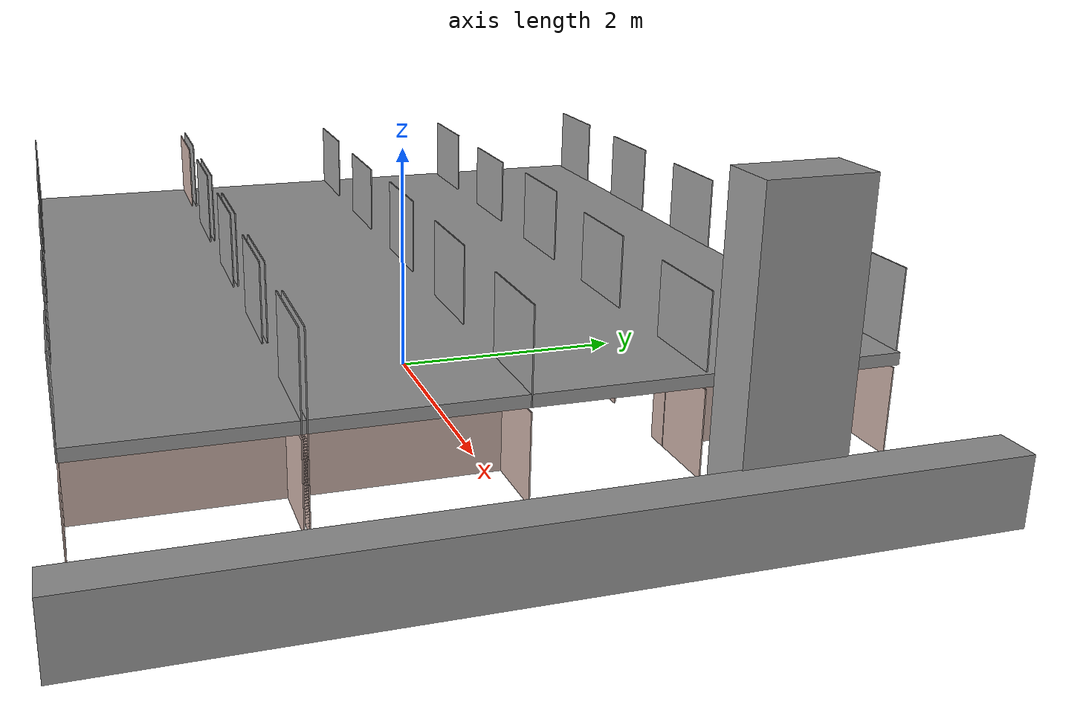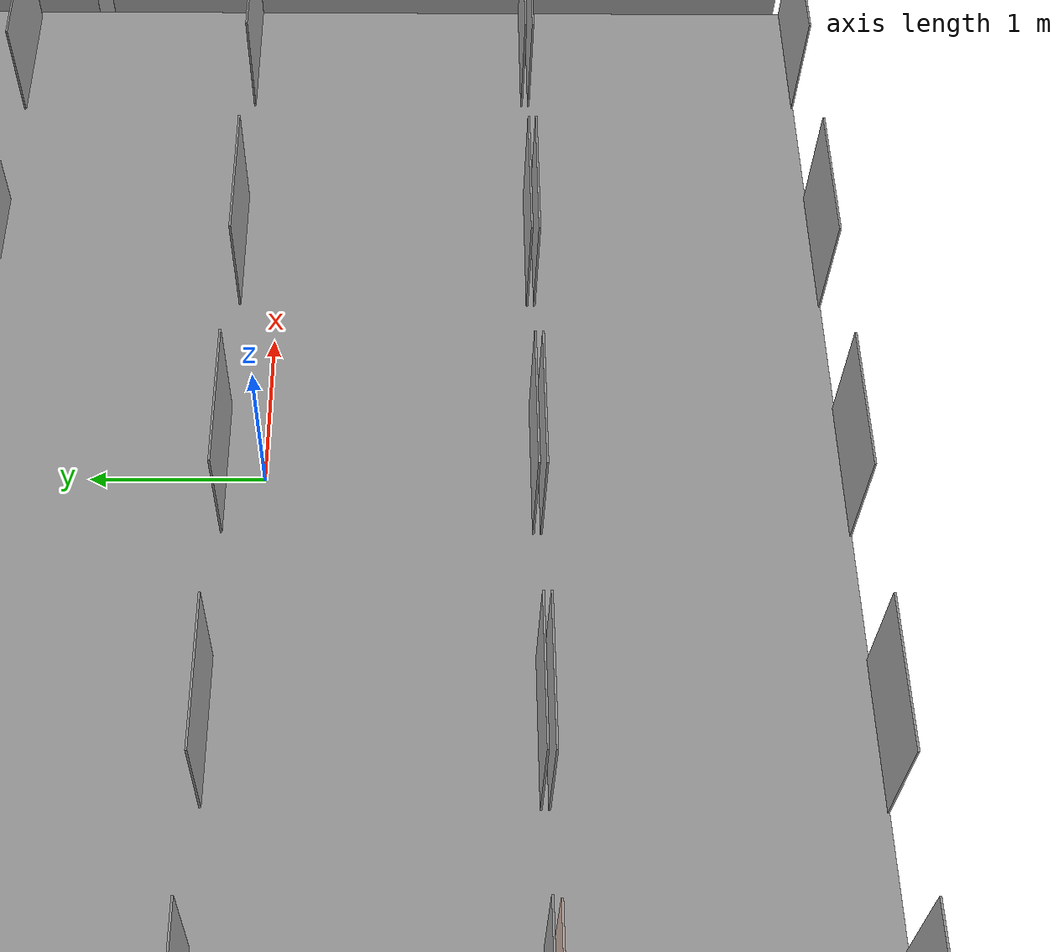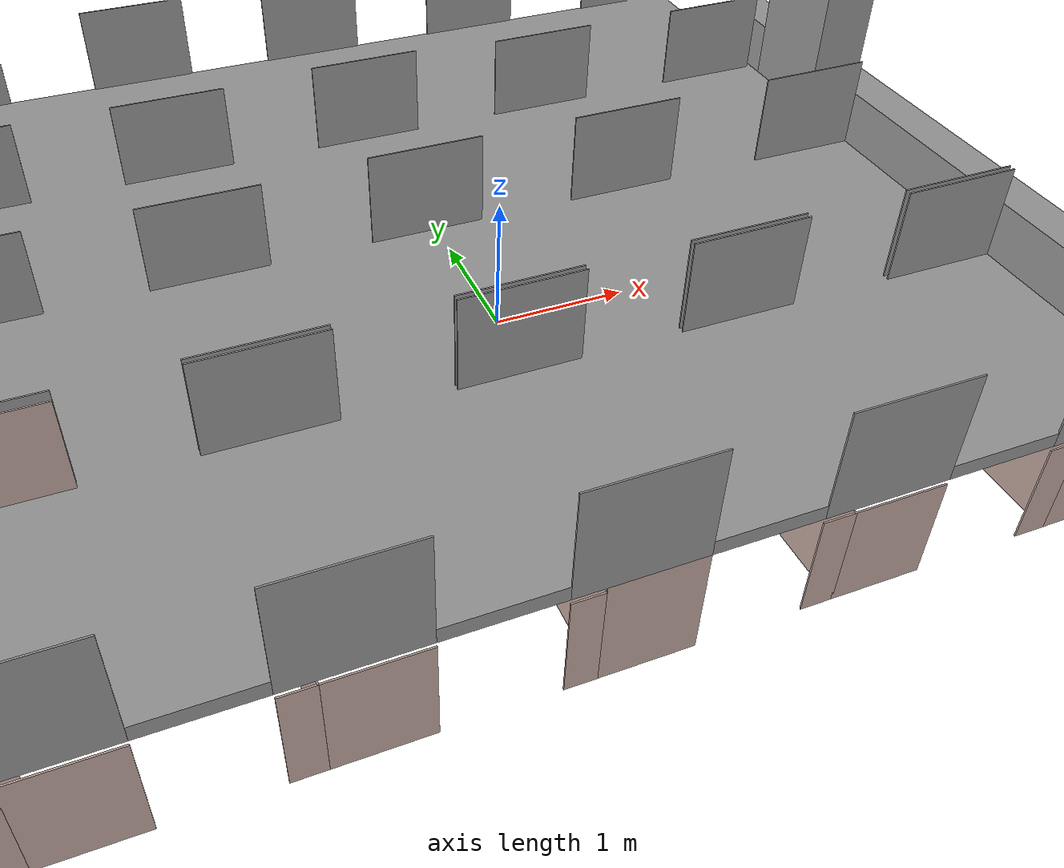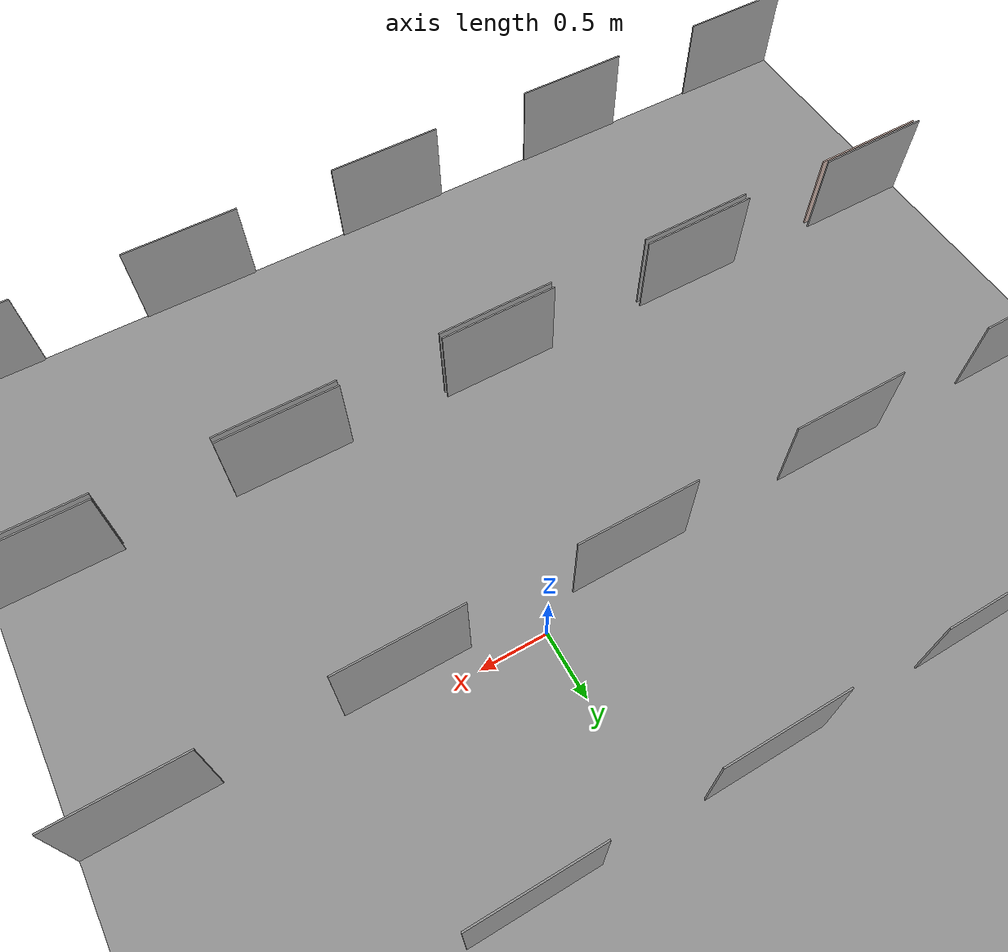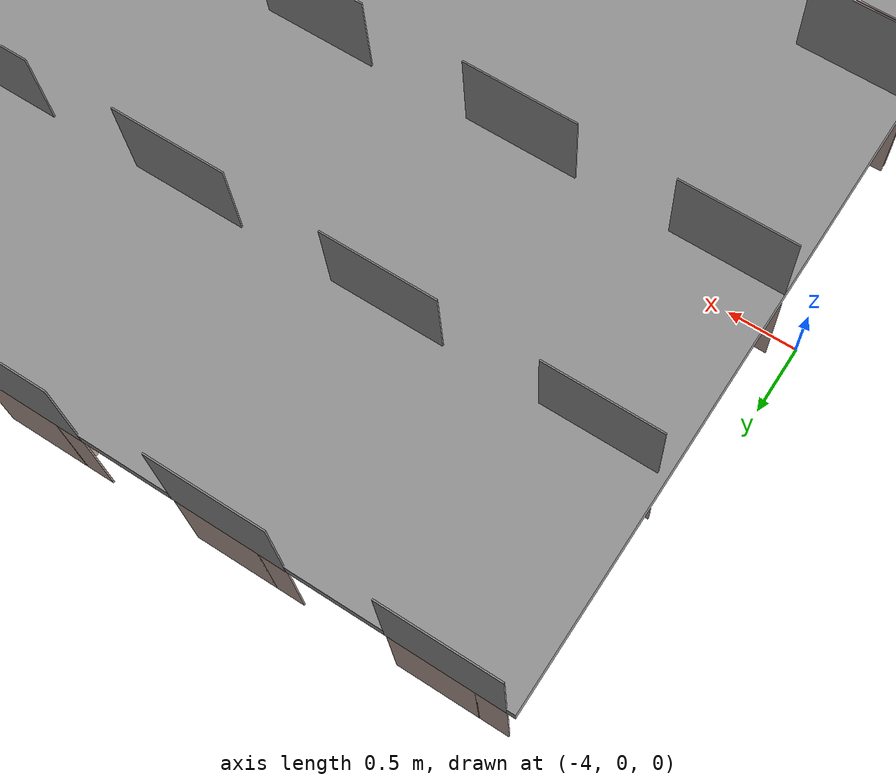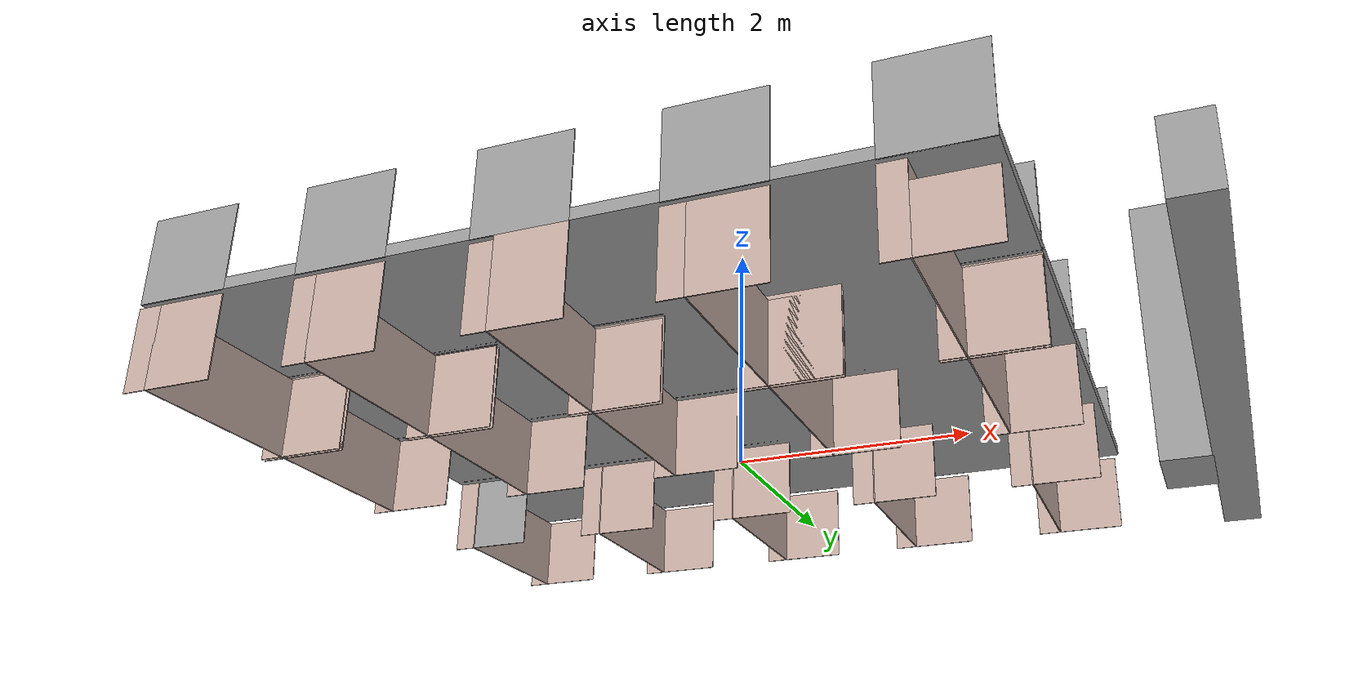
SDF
<?xml version='1.0'?>
<sdf version='1.6'>
  <model name='change_class2'>
    <pose frame=''>0.163402 0.008075 0 0 -0 0</pose>
    <link name='Floor_2'>
      <collision name='Floor_2_Collision'>
        <geometry>
          <box>
            <size>6.752 6.134 0.1</size>
          </box>
        </geometry>
        <pose frame=''>0 0 0.05 0 -0 0</pose>
      </collision>
      <visual name='Floor_2_Visual'>
        <pose frame=''>0 0 0.05 0 -0 0</pose>
        <geometry>
          <box>
            <size>6.752 6.134 0.1</size>
          </box>
        </geometry>
        <material>
          <script>
            <uri>file://media/materials/scripts/gazebo.material</uri>
            <name>Gazebo/Grey</name>
          </script>
          <ambient>1 1 1 1</ambient>
        </material>
      </visual>
      <pose frame=''>-0.632402 -0.013075 0.751 0 -0 0</pose>
    </link>
    <link name='Wall_10'>
      <collision name='Wall_10_Collision'>
        <geometry>
          <box>
            <size>0.598 0.01 0.715</size>
          </box>
        </geometry>
        <pose frame=''>0 0 0.3575 0 -0 0</pose>
      </collision>
      <visual name='Wall_10_Visual'>
        <pose frame=''>0 0 0.3575 0 -0 0</pose>
        <geometry>
          <box>
            <size>0.598 0.01 0.715</size>
          </box>
        </geometry>
        <material>
          <script>
            <uri>file://media/materials/scripts/gazebo.material</uri>
            <name>Gazebo/Grey</name>
          </script>
          <ambient>0.760784 0.662745 0.627451 1</ambient>
        </material>
      </visual>
      <pose frame=''>-0.535402 1.46893 0 0 -0 0</pose>
    </link>
    <link name='Wall_12'>
      <collision name='Wall_12_Collision'>
        <geometry>
          <box>
            <size>0.598 0.01 0.715</size>
          </box>
        </geometry>
        <pose frame=''>0 0 0.3575 0 -0 0</pose>
      </collision>
      <visual name='Wall_12_Visual'>
        <pose frame=''>0 0 0.3575 0 -0 0</pose>
        <geometry>
          <box>
            <size>0.598 0.01 0.715</size>
          </box>
        </geometry>
        <material>
          <script>
            <uri>file://media/materials/scripts/gazebo.material</uri>
            <name>Gazebo/Grey</name>
          </script>
          <ambient>0.760784 0.662745 0.627451 1</ambient>
        </material>
      </visual>
      <pose frame=''>0.901598 1.46893 0 0 -0 0</pose>
    </link>
    <link name='Wall_138'>
      <collision name='Wall_138_Collision'>
        <geometry>
          <box>
            <size>0.593 0.01 0.715</size>
          </box>
        </geometry>
        <pose frame=''>0 0 0.3575 0 -0 0</pose>
      </collision>
      <visual name='Wall_138_Visual'>
        <pose frame=''>0 0 0.3575 0 -0 0</pose>
        <geometry>
          <box>
            <size>0.593 0.01 0.715</size>
          </box>
        </geometry>
        <material>
          <script>
            <uri>file://media/materials/scripts/gazebo.material</uri>
            <name>Gazebo/Grey</name>
          </script>
          <ambient>0.760784 0.662745 0.627451 1</ambient>
        </material>
      </visual>
      <pose frame=''>-3.4519 3.04292 0 0 -0 0</pose>
    </link>
    <link name='Wall_14'>
      <collision name='Wall_14_Collision'>
        <geometry>
          <box>
            <size>0.61 0.01 0.715</size>
          </box>
        </geometry>
        <pose frame=''>0 0 0.3575 0 -0 0</pose>
      </collision>
      <visual name='Wall_14_Visual'>
        <pose frame=''>0 0 0.3575 0 -0 0</pose>
        <geometry>
          <box>
            <size>0.61 0.01 0.715</size>
          </box>
        </geometry>
        <material>
          <script>
            <uri>file://media/materials/scripts/gazebo.material</uri>
            <name>Gazebo/Grey</name>
          </script>
          <ambient>0.760784 0.662745 0.627451 1</ambient>
        </material>
      </visual>
      <pose frame=''>2.3996 1.46893 0 0 -0 0</pose>
    </link>
    <link name='Wall_140'>
      <collision name='Wall_140_Collision'>
        <geometry>
          <box>
            <size>0.598 0.01 0.715</size>
          </box>
        </geometry>
        <pose frame=''>0 0 0.3575 0 -0 0</pose>
      </collision>
      <visual name='Wall_140_Visual'>
        <pose frame=''>0 0 0.3575 0 -0 0</pose>
        <geometry>
          <box>
            <size>0.598 0.01 0.715</size>
          </box>
        </geometry>
        <material>
          <script>
            <uri>file://media/materials/scripts/gazebo.material</uri>
            <name>Gazebo/Grey</name>
          </script>
          <ambient>0.760784 0.662745 0.627451 1</ambient>
        </material>
      </visual>
      <pose frame=''>-1.9864 3.04292 0 0 -0 0</pose>
    </link>
    <link name='Wall_143'>
      <collision name='Wall_143_Collision'>
        <geometry>
          <box>
            <size>0.598 0.01 0.715</size>
          </box>
        </geometry>
        <pose frame=''>0 0 0.3575 0 -0 0</pose>
      </collision>
      <visual name='Wall_143_Visual'>
        <pose frame=''>0 0 0.3575 0 -0 0</pose>
        <geometry>
          <box>
            <size>0.598 0.01 0.715</size>
          </box>
        </geometry>
        <material>
          <script>
            <uri>file://media/materials/scripts/gazebo.material</uri>
            <name>Gazebo/Grey</name>
          </script>
          <ambient>0.760784 0.662745 0.627451 1</ambient>
        </material>
      </visual>
      <pose frame=''>-0.535402 3.04292 0 0 -0 0</pose>
    </link>
    <link name='Wall_147'>
      <collision name='Wall_147_Collision'>
        <geometry>
          <box>
            <size>0.598 0.01 0.715</size>
          </box>
        </geometry>
        <pose frame=''>0 0 0.3575 0 -0 0</pose>
      </collision>
      <visual name='Wall_147_Visual'>
        <pose frame=''>0 0 0.3575 0 -0 0</pose>
        <geometry>
          <box>
            <size>0.598 0.01 0.715</size>
          </box>
        </geometry>
        <material>
          <script>
            <uri>file://media/materials/scripts/gazebo.material</uri>
            <name>Gazebo/Grey</name>
          </script>
          <ambient>0.760784 0.662745 0.627451 1</ambient>
        </material>
      </visual>
      <pose frame=''>0.901598 3.04292 0 0 -0 0</pose>
    </link>
    <link name='Wall_153'>
      <collision name='Wall_153_Collision'>
        <geometry>
          <box>
            <size>0.609517 0.01 0.715</size>
          </box>
        </geometry>
        <pose frame=''>0 0 0.3575 0 -0 0</pose>
      </collision>
      <visual name='Wall_153_Visual'>
        <pose frame=''>0 0 0.3575 0 -0 0</pose>
        <geometry>
          <box>
            <size>0.609517 0.01 0.715</size>
          </box>
        </geometry>
        <material>
          <script>
            <uri>file://media/materials/scripts/gazebo.material</uri>
            <name>Gazebo/Grey</name>
          </script>
          <ambient>0.760784 0.662745 0.627451 1</ambient>
        </material>
      </visual>
      <pose frame=''>2.3996 3.04292 0 0 -0 0</pose>
    </link>
    <link name='Wall_155'>
      <collision name='Wall_155_Collision'>
        <geometry>
          <box>
            <size>0.798 0.01 0.715</size>
          </box>
        </geometry>
        <pose frame=''>0 0 0.3575 0 -0 0</pose>
      </collision>
      <visual name='Wall_155_Visual'>
        <pose frame=''>0 0 0.3575 0 -0 0</pose>
        <geometry>
          <box>
            <size>0.798 0.01 0.715</size>
          </box>
        </geometry>
        <material>
          <script>
            <uri>file://media/materials/scripts/gazebo.material</uri>
            <name>Gazebo/Grey</name>
          </script>
          <ambient>1 1 1 1</ambient>
        </material>
      </visual>
      <pose frame=''>-3.5494 1.46893 0.751 0 -0 0</pose>
    </link>
    <link name='Wall_156'>
      <collision name='Wall_156_Collision'>
        <geometry>
          <box>
            <size>0.798 0.01 0.715</size>
          </box>
        </geometry>
        <pose frame=''>0 0 0.3575 0 -0 0</pose>
      </collision>
      <visual name='Wall_156_Visual'>
        <pose frame=''>0 0 0.3575 0 -0 0</pose>
        <geometry>
          <box>
            <size>0.798 0.01 0.715</size>
          </box>
        </geometry>
        <material>
          <script>
            <uri>file://media/materials/scripts/gazebo.material</uri>
            <name>Gazebo/Grey</name>
          </script>
          <ambient>1 1 1 1</ambient>
        </material>
      </visual>
      <pose frame=''>-2.0904 1.46893 0.751 0 -0 0</pose>
    </link>
    <link name='Wall_157'>
      <collision name='Wall_157_Collision'>
        <geometry>
          <box>
            <size>0.798 0.01 0.751</size>
          </box>
        </geometry>
        <pose frame=''>0 0 0.3755 0 -0 0</pose>
      </collision>
      <visual name='Wall_157_Visual'>
        <pose frame=''>0 0 0.3755 0 -0 0</pose>
        <geometry>
          <box>
            <size>0.798 0.01 0.751</size>
          </box>
        </geometry>
        <material>
          <script>
            <uri>file://media/materials/scripts/gazebo.material</uri>
            <name>Gazebo/Grey</name>
          </script>
          <ambient>1 1 1 1</ambient>
        </material>
      </visual>
      <pose frame=''>-0.639402 1.46893 0.751 0 -0 0</pose>
    </link>
    <link name='Wall_158'>
      <collision name='Wall_158_Collision'>
        <geometry>
          <box>
            <size>0.798 0.01 0.715</size>
          </box>
        </geometry>
        <pose frame=''>0 0 0.3575 0 -0 0</pose>
      </collision>
      <visual name='Wall_158_Visual'>
        <pose frame=''>0 0 0.3575 0 -0 0</pose>
        <geometry>
          <box>
            <size>0.798 0.01 0.715</size>
          </box>
        </geometry>
        <material>
          <script>
            <uri>file://media/materials/scripts/gazebo.material</uri>
            <name>Gazebo/Grey</name>
          </script>
          <ambient>1 1 1 1</ambient>
        </material>
      </visual>
      <pose frame=''>0.801598 1.46893 0.751 0 -0 0</pose>
    </link>
    <link name='Wall_159'>
      <collision name='Wall_159_Collision'>
        <geometry>
          <box>
            <size>0.798 0.01 0.715</size>
          </box>
        </geometry>
        <pose frame=''>0 0 0.3575 0 -0 0</pose>
      </collision>
      <visual name='Wall_159_Visual'>
        <pose frame=''>0 0 0.3575 0 -0 0</pose>
        <geometry>
          <box>
            <size>0.798 0.01 0.715</size>
          </box>
        </geometry>
        <material>
          <script>
            <uri>file://media/materials/scripts/gazebo.material</uri>
            <name>Gazebo/Grey</name>
          </script>
          <ambient>1 1 1 1</ambient>
        </material>
      </visual>
      <pose frame=''>2.3056 1.46893 0.751 0 -0 0</pose>
    </link>
    <link name='Wall_16'>
      <collision name='Wall_16_Collision'>
        <geometry>
          <box>
            <size>0.598 0.01 0.715</size>
          </box>
        </geometry>
        <pose frame=''>0 0 0.3575 0 -0 0</pose>
      </collision>
      <visual name='Wall_16_Visual'>
        <pose frame=''>0 0 0.3575 0 -0 0</pose>
        <geometry>
          <box>
            <size>0.598 0.01 0.715</size>
          </box>
        </geometry>
        <material>
          <script>
            <uri>file://media/materials/scripts/gazebo.material</uri>
            <name>Gazebo/Grey</name>
          </script>
          <ambient>0.760784 0.662745 0.627451 1</ambient>
        </material>
      </visual>
      <pose frame=''>-3.5094 0.108925 0 0 -0 0</pose>
    </link>
    <link name='Wall_160'>
      <collision name='Wall_160_Collision'>
        <geometry>
          <box>
            <size>0.798 0.01 0.715</size>
          </box>
        </geometry>
        <pose frame=''>0 0 0.3575 0 -0 0</pose>
      </collision>
      <visual name='Wall_160_Visual'>
        <pose frame=''>0 0 0.3575 0 -0 0</pose>
        <geometry>
          <box>
            <size>0.798 0.01 0.715</size>
          </box>
        </geometry>
        <material>
          <script>
            <uri>file://media/materials/scripts/gazebo.material</uri>
            <name>Gazebo/Grey</name>
          </script>
          <ambient>1 1 1 1</ambient>
        </material>
      </visual>
      <pose frame=''>-3.6094 0.108925 0.751 0 -0 0</pose>
    </link>
    <link name='Wall_161'>
      <collision name='Wall_161_Collision'>
        <geometry>
          <box>
            <size>0.797 0.01 0.715</size>
          </box>
        </geometry>
        <pose frame=''>0 0 0.3575 0 -0 0</pose>
      </collision>
      <visual name='Wall_161_Visual'>
        <pose frame=''>0 0 0.3575 0 -0 0</pose>
        <geometry>
          <box>
            <size>0.797 0.01 0.715</size>
          </box>
        </geometry>
        <material>
          <script>
            <uri>file://media/materials/scripts/gazebo.material</uri>
            <name>Gazebo/Grey</name>
          </script>
          <ambient>1 1 1 1</ambient>
        </material>
      </visual>
      <pose frame=''>-2.1499 0.104925 0.751 0 -0 0</pose>
    </link>
    <link name='Wall_162'>
      <collision name='Wall_162_Collision'>
        <geometry>
          <box>
            <size>0.798 0.01 0.751</size>
          </box>
        </geometry>
        <pose frame=''>0 0 0.3755 0 -0 0</pose>
      </collision>
      <visual name='Wall_162_Visual'>
        <pose frame=''>0 0 0.3755 0 -0 0</pose>
        <geometry>
          <box>
            <size>0.798 0.01 0.751</size>
          </box>
        </geometry>
        <material>
          <script>
            <uri>file://media/materials/scripts/gazebo.material</uri>
            <name>Gazebo/Grey</name>
          </script>
          <ambient>1 1 1 1</ambient>
        </material>
      </visual>
      <pose frame=''>-0.647402 0.108925 0.751 0 -0 0</pose>
    </link>
    <link name='Wall_163'>
      <collision name='Wall_163_Collision'>
        <geometry>
          <box>
            <size>0.798 0.01 0.751</size>
          </box>
        </geometry>
        <pose frame=''>0 0 0.3755 0 -0 0</pose>
      </collision>
      <visual name='Wall_163_Visual'>
        <pose frame=''>0 0 0.3755 0 -0 0</pose>
        <geometry>
          <box>
            <size>0.798 0.01 0.751</size>
          </box>
        </geometry>
        <material>
          <script>
            <uri>file://media/materials/scripts/gazebo.material</uri>
            <name>Gazebo/Grey</name>
          </script>
          <ambient>1 1 1 1</ambient>
        </material>
      </visual>
      <pose frame=''>2.3446 0.108925 0.751 0 -0 0</pose>
    </link>
    <link name='Wall_164'>
      <collision name='Wall_164_Collision'>
        <geometry>
          <box>
            <size>0.798 0.01 0.751</size>
          </box>
        </geometry>
        <pose frame=''>0 0 0.3755 0 -0 0</pose>
      </collision>
      <visual name='Wall_164_Visual'>
        <pose frame=''>0 0 0.3755 0 -0 0</pose>
        <geometry>
          <box>
            <size>0.798 0.01 0.751</size>
          </box>
        </geometry>
        <material>
          <script>
            <uri>file://media/materials/scripts/gazebo.material</uri>
            <name>Gazebo/Grey</name>
          </script>
          <ambient>1 1 1 1</ambient>
        </material>
      </visual>
      <pose frame=''>-3.6094 -1.47107 0.751 0 -0 0</pose>
    </link>
    <link name='Wall_165'>
      <collision name='Wall_165_Collision'>
        <geometry>
          <box>
            <size>0.798 0.01 0.751</size>
          </box>
        </geometry>
        <pose frame=''>0 0 0.3755 0 -0 0</pose>
      </collision>
      <visual name='Wall_165_Visual'>
        <pose frame=''>0 0 0.3755 0 -0 0</pose>
        <geometry>
          <box>
            <size>0.798 0.01 0.751</size>
          </box>
        </geometry>
        <material>
          <script>
            <uri>file://media/materials/scripts/gazebo.material</uri>
            <name>Gazebo/Grey</name>
          </script>
          <ambient>1 1 1 1</ambient>
        </material>
      </visual>
      <pose frame=''>-2.1534 -1.47107 0.751 0 -0 0</pose>
    </link>
    <link name='Wall_166'>
      <collision name='Wall_166_Collision'>
        <geometry>
          <box>
            <size>0.798 0.01 0.751</size>
          </box>
        </geometry>
        <pose frame=''>0 0 0.3755 0 -0 0</pose>
      </collision>
      <visual name='Wall_166_Visual'>
        <pose frame=''>0 0 0.3755 0 -0 0</pose>
        <geometry>
          <box>
            <size>0.798 0.01 0.751</size>
          </box>
        </geometry>
        <material>
          <script>
            <uri>file://media/materials/scripts/gazebo.material</uri>
            <name>Gazebo/Grey</name>
          </script>
          <ambient>1 1 1 1</ambient>
        </material>
      </visual>
      <pose frame=''>-0.649402 -1.47107 0.751 0 -0 0</pose>
    </link>
    <link name='Wall_167'>
      <collision name='Wall_167_Collision'>
        <geometry>
          <box>
            <size>0.798 0.01 0.751</size>
          </box>
        </geometry>
        <pose frame=''>0 0 0.3755 0 -0 0</pose>
      </collision>
      <visual name='Wall_167_Visual'>
        <pose frame=''>0 0 0.3755 0 -0 0</pose>
        <geometry>
          <box>
            <size>0.798 0.01 0.751</size>
          </box>
        </geometry>
        <material>
          <script>
            <uri>file://media/materials/scripts/gazebo.material</uri>
            <name>Gazebo/Grey</name>
          </script>
          <ambient>1 1 1 1</ambient>
        </material>
      </visual>
      <pose frame=''>0.830598 0.104925 0.751 0 -0 0</pose>
    </link>
    <link name='Wall_168'>
      <collision name='Wall_168_Collision'>
        <geometry>
          <box>
            <size>0.798 0.01 0.751</size>
          </box>
        </geometry>
        <pose frame=''>0 0 0.3755 0 -0 0</pose>
      </collision>
      <visual name='Wall_168_Visual'>
        <pose frame=''>0 0 0.3755 0 -0 0</pose>
        <geometry>
          <box>
            <size>0.798 0.01 0.751</size>
          </box>
        </geometry>
        <material>
          <script>
            <uri>file://media/materials/scripts/gazebo.material</uri>
            <name>Gazebo/Grey</name>
          </script>
          <ambient>1 1 1 1</ambient>
        </material>
      </visual>
      <pose frame=''>0.831598 -1.51107 0.751 0 -0 0</pose>
    </link>
    <link name='Wall_169'>
      <collision name='Wall_169_Collision'>
        <geometry>
          <box>
            <size>0.798 0.01 0.751</size>
          </box>
        </geometry>
        <pose frame=''>0 0 0.3755 0 -0 0</pose>
      </collision>
      <visual name='Wall_169_Visual'>
        <pose frame=''>0 0 0.3755 0 -0 0</pose>
        <geometry>
          <box>
            <size>0.798 0.01 0.751</size>
          </box>
        </geometry>
        <material>
          <script>
            <uri>file://media/materials/scripts/gazebo.material</uri>
            <name>Gazebo/Grey</name>
          </script>
          <ambient>1 1 1 1</ambient>
        </material>
      </visual>
      <pose frame=''>2.3446 -1.47107 0.751 0 -0 0</pose>
    </link>
    <link name='Wall_170'>
      <collision name='Wall_170_Collision'>
        <geometry>
          <box>
            <size>0.798 0.01 0.751</size>
          </box>
        </geometry>
        <pose frame=''>0 0 0.3755 0 -0 0</pose>
      </collision>
      <visual name='Wall_170_Visual'>
        <pose frame=''>0 0 0.3755 0 -0 0</pose>
        <geometry>
          <box>
            <size>0.798 0.01 0.751</size>
          </box>
        </geometry>
        <material>
          <script>
            <uri>file://media/materials/scripts/gazebo.material</uri>
            <name>Gazebo/Grey</name>
          </script>
          <ambient>1 1 1 1</ambient>
        </material>
      </visual>
      <pose frame=''>2.3446 -1.47107 0.751 0 -0 0</pose>
    </link>
    <link name='Wall_171'>
      <collision name='Wall_171_Collision'>
        <geometry>
          <box>
            <size>0.798 0.01 0.751</size>
          </box>
        </geometry>
        <pose frame=''>0 0 0.3755 0 -0 0</pose>
      </collision>
      <visual name='Wall_171_Visual'>
        <pose frame=''>0 0 0.3755 0 -0 0</pose>
        <geometry>
          <box>
            <size>0.798 0.01 0.751</size>
          </box>
        </geometry>
        <material>
          <script>
            <uri>file://media/materials/scripts/gazebo.material</uri>
            <name>Gazebo/Grey</name>
          </script>
          <ambient>1 1 1 1</ambient>
        </material>
      </visual>
      <pose frame=''>2.3446 -1.51107 0.751 0 -0 0</pose>
    </link>
    <link name='Wall_172'>
      <collision name='Wall_172_Collision'>
        <geometry>
          <box>
            <size>0.798 0.01 0.751</size>
          </box>
        </geometry>
        <pose frame=''>0 0 0.3755 0 -0 0</pose>
      </collision>
      <visual name='Wall_172_Visual'>
        <pose frame=''>0 0 0.3755 0 -0 0</pose>
        <geometry>
          <box>
            <size>0.798 0.01 0.751</size>
          </box>
        </geometry>
        <material>
          <script>
            <uri>file://media/materials/scripts/gazebo.material</uri>
            <name>Gazebo/Grey</name>
          </script>
          <ambient>1 1 1 1</ambient>
        </material>
      </visual>
      <pose frame=''>0.831598 -1.51107 0.751 0 -0 0</pose>
    </link>
    <link name='Wall_173'>
      <collision name='Wall_173_Collision'>
        <geometry>
          <box>
            <size>0.798 0.01 0.751</size>
          </box>
        </geometry>
        <pose frame=''>0 0 0.3755 0 -0 0</pose>
      </collision>
      <visual name='Wall_173_Visual'>
        <pose frame=''>0 0 0.3755 0 -0 0</pose>
        <geometry>
          <box>
            <size>0.798 0.01 0.751</size>
          </box>
        </geometry>
        <material>
          <script>
            <uri>file://media/materials/scripts/gazebo.material</uri>
            <name>Gazebo/Grey</name>
          </script>
          <ambient>1 1 1 1</ambient>
        </material>
      </visual>
      <pose frame=''>0.831598 -1.51107 0.751 0 -0 0</pose>
    </link>
    <link name='Wall_174'>
      <collision name='Wall_174_Collision'>
        <geometry>
          <box>
            <size>0.798 0.01 0.751</size>
          </box>
        </geometry>
        <pose frame=''>0 0 0.3755 0 -0 0</pose>
      </collision>
      <visual name='Wall_174_Visual'>
        <pose frame=''>0 0 0.3755 0 -0 0</pose>
        <geometry>
          <box>
            <size>0.798 0.01 0.751</size>
          </box>
        </geometry>
        <material>
          <script>
            <uri>file://media/materials/scripts/gazebo.material</uri>
            <name>Gazebo/Grey</name>
          </script>
          <ambient>1 1 1 1</ambient>
        </material>
      </visual>
      <pose frame=''>0.831598 -1.47107 0.751 0 -0 0</pose>
    </link>
    <link name='Wall_175'>
      <collision name='Wall_175_Collision'>
        <geometry>
          <box>
            <size>0.798 0.01 0.751</size>
          </box>
        </geometry>
        <pose frame=''>0 0 0.3755 0 -0 0</pose>
      </collision>
      <visual name='Wall_175_Visual'>
        <pose frame=''>0 0 0.3755 0 -0 0</pose>
        <geometry>
          <box>
            <size>0.798 0.01 0.751</size>
          </box>
        </geometry>
        <material>
          <script>
            <uri>file://media/materials/scripts/gazebo.material</uri>
            <name>Gazebo/Grey</name>
          </script>
          <ambient>1 1 1 1</ambient>
        </material>
      </visual>
      <pose frame=''>-0.649402 -1.47107 0.751 0 -0 0</pose>
    </link>
    <link name='Wall_176'>
      <collision name='Wall_176_Collision'>
        <geometry>
          <box>
            <size>0.798 0.01 0.751</size>
          </box>
        </geometry>
        <pose frame=''>0 0 0.3755 0 -0 0</pose>
      </collision>
      <visual name='Wall_176_Visual'>
        <pose frame=''>0 0 0.3755 0 -0 0</pose>
        <geometry>
          <box>
            <size>0.798 0.01 0.751</size>
          </box>
        </geometry>
        <material>
          <script>
            <uri>file://media/materials/scripts/gazebo.material</uri>
            <name>Gazebo/Grey</name>
          </script>
          <ambient>1 1 1 1</ambient>
        </material>
      </visual>
      <pose frame=''>-0.649402 -1.51107 0.751 0 -0 0</pose>
    </link>
    <link name='Wall_177'>
      <collision name='Wall_177_Collision'>
        <geometry>
          <box>
            <size>0.798 0.01 0.751</size>
          </box>
        </geometry>
        <pose frame=''>0 0 0.3755 0 -0 0</pose>
      </collision>
      <visual name='Wall_177_Visual'>
        <pose frame=''>0 0 0.3755 0 -0 0</pose>
        <geometry>
          <box>
            <size>0.798 0.01 0.751</size>
          </box>
        </geometry>
        <material>
          <script>
            <uri>file://media/materials/scripts/gazebo.material</uri>
            <name>Gazebo/Grey</name>
          </script>
          <ambient>1 1 1 1</ambient>
        </material>
      </visual>
      <pose frame=''>-2.1534 -1.51107 0.751 0 -0 0</pose>
    </link>
    <link name='Wall_178'>
      <collision name='Wall_178_Collision'>
        <geometry>
          <box>
            <size>0.798 0.01 0.751</size>
          </box>
        </geometry>
        <pose frame=''>0 0 0.3755 0 -0 0</pose>
      </collision>
      <visual name='Wall_178_Visual'>
        <pose frame=''>0 0 0.3755 0 -0 0</pose>
        <geometry>
          <box>
            <size>0.798 0.01 0.751</size>
          </box>
        </geometry>
        <material>
          <script>
            <uri>file://media/materials/scripts/gazebo.material</uri>
            <name>Gazebo/Grey</name>
          </script>
          <ambient>1 1 1 1</ambient>
        </material>
      </visual>
      <pose frame=''>-3.6094 -1.47107 0.751 0 -0 0</pose>
    </link>
    <link name='Wall_179'>
      <collision name='Wall_179_Collision'>
        <geometry>
          <box>
            <size>0.798 0.01 0.715</size>
          </box>
        </geometry>
        <pose frame=''>0 0 0.3575 0 -0 0</pose>
      </collision>
      <visual name='Wall_179_Visual'>
        <pose frame=''>0 0 0.3575 0 -0 0</pose>
        <geometry>
          <box>
            <size>0.798 0.01 0.715</size>
          </box>
        </geometry>
        <material>
          <script>
            <uri>file://media/materials/scripts/gazebo.material</uri>
            <name>Gazebo/Grey</name>
          </script>
          <ambient>0.760784 0.662745 0.627451 1</ambient>
        </material>
      </visual>
      <pose frame=''>-3.6094 -1.51307 0.751 0 -0 0</pose>
    </link>
    <link name='Wall_18'>
      <collision name='Wall_18_Collision'>
        <geometry>
          <box>
            <size>0.598 0.01 0.715</size>
          </box>
        </geometry>
        <pose frame=''>0 0 0.3575 0 -0 0</pose>
      </collision>
      <visual name='Wall_18_Visual'>
        <pose frame=''>0 0 0.3575 0 -0 0</pose>
        <geometry>
          <box>
            <size>0.598 0.01 0.715</size>
          </box>
        </geometry>
        <material>
          <script>
            <uri>file://media/materials/scripts/gazebo.material</uri>
            <name>Gazebo/Grey</name>
          </script>
          <ambient>0.760784 0.662745 0.627451 1</ambient>
        </material>
      </visual>
      <pose frame=''>-2.0494 0.108925 0 0 -0 0</pose>
    </link>
    <link name='Wall_180'>
      <collision name='Wall_180_Collision'>
        <geometry>
          <box>
            <size>0.798 0.01 0.751</size>
          </box>
        </geometry>
        <pose frame=''>0 0 0.3755 0 -0 0</pose>
      </collision>
      <visual name='Wall_180_Visual'>
        <pose frame=''>0 0 0.3755 0 -0 0</pose>
        <geometry>
          <box>
            <size>0.798 0.01 0.751</size>
          </box>
        </geometry>
        <material>
          <script>
            <uri>file://media/materials/scripts/gazebo.material</uri>
            <name>Gazebo/Grey</name>
          </script>
          <ambient>1 1 1 1</ambient>
        </material>
      </visual>
      <pose frame=''>-3.6094 -3.07508 0.751 0 -0 0</pose>
    </link>
    <link name='Wall_181'>
      <collision name='Wall_181_Collision'>
        <geometry>
          <box>
            <size>0.798 0.01 0.751</size>
          </box>
        </geometry>
        <pose frame=''>0 0 0.3755 0 -0 0</pose>
      </collision>
      <visual name='Wall_181_Visual'>
        <pose frame=''>0 0 0.3755 0 -0 0</pose>
        <geometry>
          <box>
            <size>0.798 0.01 0.751</size>
          </box>
        </geometry>
        <material>
          <script>
            <uri>file://media/materials/scripts/gazebo.material</uri>
            <name>Gazebo/Grey</name>
          </script>
          <ambient>1 1 1 1</ambient>
        </material>
      </visual>
      <pose frame=''>-2.1534 -3.07508 0.751 0 -0 0</pose>
    </link>
    <link name='Wall_182'>
      <collision name='Wall_182_Collision'>
        <geometry>
          <box>
            <size>0.798 0.01 0.751</size>
          </box>
        </geometry>
        <pose frame=''>0 0 0.3755 0 -0 0</pose>
      </collision>
      <visual name='Wall_182_Visual'>
        <pose frame=''>0 0 0.3755 0 -0 0</pose>
        <geometry>
          <box>
            <size>0.798 0.01 0.751</size>
          </box>
        </geometry>
        <material>
          <script>
            <uri>file://media/materials/scripts/gazebo.material</uri>
            <name>Gazebo/Grey</name>
          </script>
          <ambient>1 1 1 1</ambient>
        </material>
      </visual>
      <pose frame=''>-0.649402 -3.07508 0.751 0 -0 0</pose>
    </link>
    <link name='Wall_183'>
      <collision name='Wall_183_Collision'>
        <geometry>
          <box>
            <size>0.798 0.01 0.751</size>
          </box>
        </geometry>
        <pose frame=''>0 0 0.3755 0 -0 0</pose>
      </collision>
      <visual name='Wall_183_Visual'>
        <pose frame=''>0 0 0.3755 0 -0 0</pose>
        <geometry>
          <box>
            <size>0.798 0.01 0.751</size>
          </box>
        </geometry>
        <material>
          <script>
            <uri>file://media/materials/scripts/gazebo.material</uri>
            <name>Gazebo/Grey</name>
          </script>
          <ambient>1 1 1 1</ambient>
        </material>
      </visual>
      <pose frame=''>0.831598 -3.07508 0.751 0 -0 0</pose>
    </link>
    <link name='Wall_184'>
      <collision name='Wall_184_Collision'>
        <geometry>
          <box>
            <size>0.798 0.01 0.751</size>
          </box>
        </geometry>
        <pose frame=''>0 0 0.3755 0 -0 0</pose>
      </collision>
      <visual name='Wall_184_Visual'>
        <pose frame=''>0 0 0.3755 0 -0 0</pose>
        <geometry>
          <box>
            <size>0.798 0.01 0.751</size>
          </box>
        </geometry>
        <material>
          <script>
            <uri>file://media/materials/scripts/gazebo.material</uri>
            <name>Gazebo/Grey</name>
          </script>
          <ambient>1 1 1 1</ambient>
        </material>
      </visual>
      <pose frame=''>2.3446 -3.07508 0.751 0 -0 0</pose>
    </link>
    <link name='Wall_185'>
      <collision name='Wall_185_Collision'>
        <geometry>
          <box>
            <size>0.798 0.01 0.751</size>
          </box>
        </geometry>
        <pose frame=''>0 0 0.3755 0 -0 0</pose>
      </collision>
      <visual name='Wall_185_Visual'>
        <pose frame=''>0 0 0.3755 0 -0 0</pose>
        <geometry>
          <box>
            <size>0.798 0.01 0.751</size>
          </box>
        </geometry>
        <material>
          <script>
            <uri>file://media/materials/scripts/gazebo.material</uri>
            <name>Gazebo/Grey</name>
          </script>
          <ambient>1 1 1 1</ambient>
        </material>
      </visual>
      <pose frame=''>-3.5494 3.04893 0.751 0 -0 0</pose>
    </link>
    <link name='Wall_186'>
      <collision name='Wall_186_Collision'>
        <geometry>
          <box>
            <size>0.798 0.01 0.751</size>
          </box>
        </geometry>
        <pose frame=''>0 0 0.3755 0 -0 0</pose>
      </collision>
      <visual name='Wall_186_Visual'>
        <pose frame=''>0 0 0.3755 0 -0 0</pose>
        <geometry>
          <box>
            <size>0.798 0.01 0.751</size>
          </box>
        </geometry>
        <material>
          <script>
            <uri>file://media/materials/scripts/gazebo.material</uri>
            <name>Gazebo/Grey</name>
          </script>
          <ambient>1 1 1 1</ambient>
        </material>
      </visual>
      <pose frame=''>-2.0864 3.04893 0.751 0 -0 0</pose>
    </link>
    <link name='Wall_187'>
      <collision name='Wall_187_Collision'>
        <geometry>
          <box>
            <size>0.798 0.01 0.751</size>
          </box>
        </geometry>
        <pose frame=''>0 0 0.3755 0 -0 0</pose>
      </collision>
      <visual name='Wall_187_Visual'>
        <pose frame=''>0 0 0.3755 0 -0 0</pose>
        <geometry>
          <box>
            <size>0.798 0.01 0.751</size>
          </box>
        </geometry>
        <material>
          <script>
            <uri>file://media/materials/scripts/gazebo.material</uri>
            <name>Gazebo/Grey</name>
          </script>
          <ambient>1 1 1 1</ambient>
        </material>
      </visual>
      <pose frame=''>-0.639402 3.04893 0.751 0 -0 0</pose>
    </link>
    <link name='Wall_188'>
      <collision name='Wall_188_Collision'>
        <geometry>
          <box>
            <size>0.798 0.01 0.751</size>
          </box>
        </geometry>
        <pose frame=''>0 0 0.3755 0 -0 0</pose>
      </collision>
      <visual name='Wall_188_Visual'>
        <pose frame=''>0 0 0.3755 0 -0 0</pose>
        <geometry>
          <box>
            <size>0.798 0.01 0.751</size>
          </box>
        </geometry>
        <material>
          <script>
            <uri>file://media/materials/scripts/gazebo.material</uri>
            <name>Gazebo/Grey</name>
          </script>
          <ambient>1 1 1 1</ambient>
        </material>
      </visual>
      <pose frame=''>0.801598 3.04893 0.751 0 -0 0</pose>
    </link>
    <link name='Wall_189'>
      <collision name='Wall_189_Collision'>
        <geometry>
          <box>
            <size>0.798 0.01 0.751</size>
          </box>
        </geometry>
        <pose frame=''>0 0 0.3755 0 -0 0</pose>
      </collision>
      <visual name='Wall_189_Visual'>
        <pose frame=''>0 0 0.3755 0 -0 0</pose>
        <geometry>
          <box>
            <size>0.798 0.01 0.751</size>
          </box>
        </geometry>
        <material>
          <script>
            <uri>file://media/materials/scripts/gazebo.material</uri>
            <name>Gazebo/Grey</name>
          </script>
          <ambient>1 1 1 1</ambient>
        </material>
      </visual>
      <pose frame=''>2.3056 3.04893 0.751 0 -0 0</pose>
    </link>
    <link name='Wall_193'>
      <collision name='Wall_193_Collision'>
        <geometry>
          <box>
            <size>1.584 0.01 0.715</size>
          </box>
        </geometry>
        <pose frame=''>0 0 0.3575 0 -0 0</pose>
      </collision>
      <visual name='Wall_193_Visual'>
        <pose frame=''>0 0 0.3575 0 -0 0</pose>
        <geometry>
          <box>
            <size>1.584 0.01 0.715</size>
          </box>
        </geometry>
        <material>
          <script>
            <uri>file://media/materials/scripts/gazebo.material</uri>
            <name>Gazebo/Grey</name>
          </script>
          <ambient>0.760784 0.662745 0.627451 1</ambient>
        </material>
      </visual>
      <pose frame=''>-2.2804 2.25592 0 0 0 -1.5708</pose>
    </link>
    <link name='Wall_195'>
      <collision name='Wall_195_Collision'>
        <geometry>
          <box>
            <size>1.584 0.01 0.715</size>
          </box>
        </geometry>
        <pose frame=''>0 0 0.3575 0 -0 0</pose>
      </collision>
      <visual name='Wall_195_Visual'>
        <pose frame=''>0 0 0.3575 0 -0 0</pose>
        <geometry>
          <box>
            <size>1.584 0.01 0.715</size>
          </box>
        </geometry>
        <material>
          <script>
            <uri>file://media/materials/scripts/gazebo.material</uri>
            <name>Gazebo/Grey</name>
          </script>
          <ambient>0.760784 0.662745 0.627451 1</ambient>
        </material>
      </visual>
      <pose frame=''>-0.829402 2.25592 0 0 0 -1.5708</pose>
    </link>
    <link name='Wall_197'>
      <collision name='Wall_197_Collision'>
        <geometry>
          <box>
            <size>1.584 0.01 0.715</size>
          </box>
        </geometry>
        <pose frame=''>0 0 0.3575 0 -0 0</pose>
      </collision>
      <visual name='Wall_197_Visual'>
        <pose frame=''>0 0 0.3575 0 -0 0</pose>
        <geometry>
          <box>
            <size>1.584 0.01 0.715</size>
          </box>
        </geometry>
        <material>
          <script>
            <uri>file://media/materials/scripts/gazebo.material</uri>
            <name>Gazebo/Grey</name>
          </script>
          <ambient>0.760784 0.662745 0.627451 1</ambient>
        </material>
      </visual>
      <pose frame=''>0.607598 2.25592 0 0 0 -1.5708</pose>
    </link>
    <link name='Wall_199'>
      <collision name='Wall_199_Collision'>
        <geometry>
          <box>
            <size>1.58405 0.01 0.715</size>
          </box>
        </geometry>
        <pose frame=''>0 0 0.3575 0 -0 0</pose>
      </collision>
      <visual name='Wall_199_Visual'>
        <pose frame=''>0 0 0.3575 0 -0 0</pose>
        <geometry>
          <box>
            <size>1.58405 0.01 0.715</size>
          </box>
        </geometry>
        <material>
          <script>
            <uri>file://media/materials/scripts/gazebo.material</uri>
            <name>Gazebo/Grey</name>
          </script>
          <ambient>0.760784 0.662745 0.627451 1</ambient>
        </material>
      </visual>
      <pose frame=''>2.0996 2.25592 0 0 0 -1.5708</pose>
    </link>
    <link name='Wall_20'>
      <collision name='Wall_20_Collision'>
        <geometry>
          <box>
            <size>0.598 0.01 0.715</size>
          </box>
        </geometry>
        <pose frame=''>0 0 0.3575 0 -0 0</pose>
      </collision>
      <visual name='Wall_20_Visual'>
        <pose frame=''>0 0 0.3575 0 -0 0</pose>
        <geometry>
          <box>
            <size>0.598 0.01 0.715</size>
          </box>
        </geometry>
        <material>
          <script>
            <uri>file://media/materials/scripts/gazebo.material</uri>
            <name>Gazebo/Grey</name>
          </script>
          <ambient>0.760784 0.662745 0.627451 1</ambient>
        </material>
      </visual>
      <pose frame=''>-0.547402 0.108925 0 0 -0 0</pose>
    </link>
    <link name='Wall_203'>
      <collision name='Wall_203_Collision'>
        <geometry>
          <box>
            <size>3.194 0.01 0.715</size>
          </box>
        </geometry>
        <pose frame=''>0 0 0.3575 0 -0 0</pose>
      </collision>
      <visual name='Wall_203_Visual'>
        <pose frame=''>0 0 0.3575 0 -0 0</pose>
        <geometry>
          <box>
            <size>3.194 0.01 0.715</size>
          </box>
        </geometry>
        <material>
          <script>
            <uri>file://media/materials/scripts/gazebo.material</uri>
            <name>Gazebo/Grey</name>
          </script>
          <ambient>0.760784 0.662745 0.627451 1</ambient>
        </material>
      </visual>
      <pose frame=''>-3.8034 -1.48307 0 0 0 -1.5708</pose>
    </link>
    <link name='Wall_205'>
      <collision name='Wall_205_Collision'>
        <geometry>
          <box>
            <size>3.194 0.01 0.715</size>
          </box>
        </geometry>
        <pose frame=''>0 0 0.3575 0 -0 0</pose>
      </collision>
      <visual name='Wall_205_Visual'>
        <pose frame=''>0 0 0.3575 0 -0 0</pose>
        <geometry>
          <box>
            <size>3.194 0.01 0.715</size>
          </box>
        </geometry>
        <material>
          <script>
            <uri>file://media/materials/scripts/gazebo.material</uri>
            <name>Gazebo/Grey</name>
          </script>
          <ambient>0.760784 0.662745 0.627451 1</ambient>
        </material>
      </visual>
      <pose frame=''>-2.3434 -1.48307 0 0 0 -1.5708</pose>
    </link>
    <link name='Wall_207'>
      <collision name='Wall_207_Collision'>
        <geometry>
          <box>
            <size>3.194 0.01 0.715</size>
          </box>
        </geometry>
        <pose frame=''>0 0 0.3575 0 -0 0</pose>
      </collision>
      <visual name='Wall_207_Visual'>
        <pose frame=''>0 0 0.3575 0 -0 0</pose>
        <geometry>
          <box>
            <size>3.194 0.01 0.715</size>
          </box>
        </geometry>
        <material>
          <script>
            <uri>file://media/materials/scripts/gazebo.material</uri>
            <name>Gazebo/Grey</name>
          </script>
          <ambient>0.760784 0.662745 0.627451 1</ambient>
        </material>
      </visual>
      <pose frame=''>-0.841402 -1.48307 0 0 0 -1.5708</pose>
    </link>
    <link name='Wall_209'>
      <collision name='Wall_209_Collision'>
        <geometry>
          <box>
            <size>3.194 0.01 0.715</size>
          </box>
        </geometry>
        <pose frame=''>0 0 0.3575 0 -0 0</pose>
      </collision>
      <visual name='Wall_209_Visual'>
        <pose frame=''>0 0 0.3575 0 -0 0</pose>
        <geometry>
          <box>
            <size>3.194 0.01 0.715</size>
          </box>
        </geometry>
        <material>
          <script>
            <uri>file://media/materials/scripts/gazebo.material</uri>
            <name>Gazebo/Grey</name>
          </script>
          <ambient>0.760784 0.662745 0.627451 1</ambient>
        </material>
      </visual>
      <pose frame=''>0.636598 -1.48307 0 0 0 -1.5708</pose>
    </link>
    <link name='Wall_211'>
      <collision name='Wall_211_Collision'>
        <geometry>
          <box>
            <size>3.194 0.01 0.715</size>
          </box>
        </geometry>
        <pose frame=''>0 0 0.3575 0 -0 0</pose>
      </collision>
      <visual name='Wall_211_Visual'>
        <pose frame=''>0 0 0.3575 0 -0 0</pose>
        <geometry>
          <box>
            <size>3.194 0.01 0.715</size>
          </box>
        </geometry>
        <material>
          <script>
            <uri>file://media/materials/scripts/gazebo.material</uri>
            <name>Gazebo/Grey</name>
          </script>
          <ambient>0.760784 0.662745 0.627451 1</ambient>
        </material>
      </visual>
      <pose frame=''>2.1506 -1.48307 0 0 0 -1.5708</pose>
    </link>
    <link name='Wall_214'>
      <collision name='Wall_214_Collision'>
        <geometry>
          <box>
            <size>0.01 0.01 0.715</size>
          </box>
        </geometry>
        <pose frame=''>0 0 0.3575 0 -0 0</pose>
      </collision>
      <visual name='Wall_214_Visual'>
        <pose frame=''>0 0 0.3575 0 -0 0</pose>
        <geometry>
          <box>
            <size>0.01 0.01 0.715</size>
          </box>
        </geometry>
        <material>
          <script>
            <uri>file://media/materials/scripts/gazebo.material</uri>
            <name>Gazebo/Grey</name>
          </script>
          <ambient>0.760784 0.662745 0.627451 1</ambient>
        </material>
      </visual>
      <pose frame=''>-3.7434 1.46893 0 0 -0 0</pose>
    </link>
    <link name='Wall_216'>
      <collision name='Wall_216_Collision'>
        <geometry>
          <box>
            <size>0.01 0.01 0.715</size>
          </box>
        </geometry>
        <pose frame=''>0 0 0.3575 0 -0 0</pose>
      </collision>
      <visual name='Wall_216_Visual'>
        <pose frame=''>0 0 0.3575 0 -0 0</pose>
        <geometry>
          <box>
            <size>0.01 0.01 0.715</size>
          </box>
        </geometry>
        <material>
          <script>
            <uri>file://media/materials/scripts/gazebo.material</uri>
            <name>Gazebo/Grey</name>
          </script>
          <ambient>0.760784 0.662745 0.627451 1</ambient>
        </material>
      </visual>
      <pose frame=''>-3.7434 1.46893 0 0 -0 0</pose>
    </link>
    <link name='Wall_218'>
      <collision name='Wall_218_Collision'>
        <geometry>
          <box>
            <size>0.01 0.01 0.715</size>
          </box>
        </geometry>
        <pose frame=''>0 0 0.3575 0 -0 0</pose>
      </collision>
      <visual name='Wall_218_Visual'>
        <pose frame=''>0 0 0.3575 0 -0 0</pose>
        <geometry>
          <box>
            <size>0.01 0.01 0.715</size>
          </box>
        </geometry>
        <material>
          <script>
            <uri>file://media/materials/scripts/gazebo.material</uri>
            <name>Gazebo/Grey</name>
          </script>
          <ambient>1 1 1 1</ambient>
        </material>
      </visual>
      <pose frame=''>-3.7434 3.04292 0 0 -0 0</pose>
    </link>
    <link name='Wall_222'>
      <collision name='Wall_222_Collision'>
        <geometry>
          <box>
            <size>1.584 0.01 0.715</size>
          </box>
        </geometry>
        <pose frame=''>0 0 0.3575 0 -0 0</pose>
      </collision>
      <visual name='Wall_222_Visual'>
        <pose frame=''>0 0 0.3575 0 -0 0</pose>
        <geometry>
          <box>
            <size>1.584 0.01 0.715</size>
          </box>
        </geometry>
        <material>
          <script>
            <uri>file://media/materials/scripts/gazebo.material</uri>
            <name>Gazebo/Grey</name>
          </script>
          <ambient>0.760784 0.662745 0.627451 1</ambient>
        </material>
      </visual>
      <pose frame=''>-3.7434 2.25592 0 0 -0 1.5708</pose>
    </link>
    <link name='Wall_224'>
      <collision name='Wall_224_Collision'>
        <geometry>
          <box>
            <size>0.21 0.01 0.715</size>
          </box>
        </geometry>
        <pose frame=''>0 0 0.3575 0 -0 0</pose>
      </collision>
      <visual name='Wall_224_Visual'>
        <pose frame=''>0 0 0.3575 0 -0 0</pose>
        <geometry>
          <box>
            <size>0.21 0.01 0.715</size>
          </box>
        </geometry>
        <material>
          <script>
            <uri>file://media/materials/scripts/gazebo.material</uri>
            <name>Gazebo/Grey</name>
          </script>
          <ambient>0.760784 0.662745 0.627451 1</ambient>
        </material>
      </visual>
      <pose frame=''>-3.8434 3.04292 0 0 -0 0</pose>
    </link>
    <link name='Wall_226'>
      <collision name='Wall_226_Collision'>
        <geometry>
          <box>
            <size>0.21 0.01 0.715</size>
          </box>
        </geometry>
        <pose frame=''>0 0 0.3575 0 -0 0</pose>
      </collision>
      <visual name='Wall_226_Visual'>
        <pose frame=''>0 0 0.3575 0 -0 0</pose>
        <geometry>
          <box>
            <size>0.21 0.01 0.715</size>
          </box>
        </geometry>
        <material>
          <script>
            <uri>file://media/materials/scripts/gazebo.material</uri>
            <name>Gazebo/Grey</name>
          </script>
          <ambient>0.760784 0.662745 0.627451 1</ambient>
        </material>
      </visual>
      <pose frame=''>-3.8434 1.46893 0 0 -0 0</pose>
    </link>
    <link name='Wall_228'>
      <collision name='Wall_228_Collision'>
        <geometry>
          <box>
            <size>0.21 0.01 0.715</size>
          </box>
        </geometry>
        <pose frame=''>0 0 0.3575 0 -0 0</pose>
      </collision>
      <visual name='Wall_228_Visual'>
        <pose frame=''>0 0 0.3575 0 -0 0</pose>
        <geometry>
          <box>
            <size>0.21 0.01 0.715</size>
          </box>
        </geometry>
        <material>
          <script>
            <uri>file://media/materials/scripts/gazebo.material</uri>
            <name>Gazebo/Grey</name>
          </script>
          <ambient>0.760784 0.662745 0.627451 1</ambient>
        </material>
      </visual>
      <pose frame=''>-2.3804 3.04292 0 0 -0 0</pose>
    </link>
    <link name='Wall_230'>
      <collision name='Wall_230_Collision'>
        <geometry>
          <box>
            <size>0.21 0.01 0.715</size>
          </box>
        </geometry>
        <pose frame=''>0 0 0.3575 0 -0 0</pose>
      </collision>
      <visual name='Wall_230_Visual'>
        <pose frame=''>0 0 0.3575 0 -0 0</pose>
        <geometry>
          <box>
            <size>0.21 0.01 0.715</size>
          </box>
        </geometry>
        <material>
          <script>
            <uri>file://media/materials/scripts/gazebo.material</uri>
            <name>Gazebo/Grey</name>
          </script>
          <ambient>0.760784 0.662745 0.627451 1</ambient>
        </material>
      </visual>
      <pose frame=''>-2.3804 1.46893 0 0 -0 0</pose>
    </link>
    <link name='Wall_232'>
      <collision name='Wall_232_Collision'>
        <geometry>
          <box>
            <size>0.21 0.01 0.715</size>
          </box>
        </geometry>
        <pose frame=''>0 0 0.3575 0 -0 0</pose>
      </collision>
      <visual name='Wall_232_Visual'>
        <pose frame=''>0 0 0.3575 0 -0 0</pose>
        <geometry>
          <box>
            <size>0.21 0.01 0.715</size>
          </box>
        </geometry>
        <material>
          <script>
            <uri>file://media/materials/scripts/gazebo.material</uri>
            <name>Gazebo/Grey</name>
          </script>
          <ambient>0.760784 0.662745 0.627451 1</ambient>
        </material>
      </visual>
      <pose frame=''>-0.929402 1.46893 0 0 -0 0</pose>
    </link>
    <link name='Wall_234'>
      <collision name='Wall_234_Collision'>
        <geometry>
          <box>
            <size>0.21 0.01 0.715</size>
          </box>
        </geometry>
        <pose frame=''>0 0 0.3575 0 -0 0</pose>
      </collision>
      <visual name='Wall_234_Visual'>
        <pose frame=''>0 0 0.3575 0 -0 0</pose>
        <geometry>
          <box>
            <size>0.21 0.01 0.715</size>
          </box>
        </geometry>
        <material>
          <script>
            <uri>file://media/materials/scripts/gazebo.material</uri>
            <name>Gazebo/Grey</name>
          </script>
          <ambient>0.760784 0.662745 0.627451 1</ambient>
        </material>
      </visual>
      <pose frame=''>-0.929402 3.04292 0 0 -0 0</pose>
    </link>
    <link name='Wall_236'>
      <collision name='Wall_236_Collision'>
        <geometry>
          <box>
            <size>0.21 0.01 0.715</size>
          </box>
        </geometry>
        <pose frame=''>0 0 0.3575 0 -0 0</pose>
      </collision>
      <visual name='Wall_236_Visual'>
        <pose frame=''>0 0 0.3575 0 -0 0</pose>
        <geometry>
          <box>
            <size>0.21 0.01 0.715</size>
          </box>
        </geometry>
        <material>
          <script>
            <uri>file://media/materials/scripts/gazebo.material</uri>
            <name>Gazebo/Grey</name>
          </script>
          <ambient>0.760784 0.662745 0.627451 1</ambient>
        </material>
      </visual>
      <pose frame=''>0.507598 1.46893 0 0 -0 0</pose>
    </link>
    <link name='Wall_238'>
      <collision name='Wall_238_Collision'>
        <geometry>
          <box>
            <size>0.21 0.01 0.715</size>
          </box>
        </geometry>
        <pose frame=''>0 0 0.3575 0 -0 0</pose>
      </collision>
      <visual name='Wall_238_Visual'>
        <pose frame=''>0 0 0.3575 0 -0 0</pose>
        <geometry>
          <box>
            <size>0.21 0.01 0.715</size>
          </box>
        </geometry>
        <material>
          <script>
            <uri>file://media/materials/scripts/gazebo.material</uri>
            <name>Gazebo/Grey</name>
          </script>
          <ambient>0.760784 0.662745 0.627451 1</ambient>
        </material>
      </visual>
      <pose frame=''>0.507598 3.04292 0 0 -0 0</pose>
    </link>
    <link name='Wall_24'>
      <collision name='Wall_24_Collision'>
        <geometry>
          <box>
            <size>0.598 0.01 0.715</size>
          </box>
        </geometry>
        <pose frame=''>0 0 0.3575 0 -0 0</pose>
      </collision>
      <visual name='Wall_24_Visual'>
        <pose frame=''>0 0 0.3575 0 -0 0</pose>
        <geometry>
          <box>
            <size>0.598 0.01 0.715</size>
          </box>
        </geometry>
        <material>
          <script>
            <uri>file://media/materials/scripts/gazebo.material</uri>
            <name>Gazebo/Grey</name>
          </script>
          <ambient>0.760784 0.662745 0.627451 1</ambient>
        </material>
      </visual>
      <pose frame=''>2.4446 0.108925 0 0 -0 0</pose>
    </link>
    <link name='Wall_240'>
      <collision name='Wall_240_Collision'>
        <geometry>
          <box>
            <size>0.198 0.01 0.715</size>
          </box>
        </geometry>
        <pose frame=''>0 0 0.3575 0 -0 0</pose>
      </collision>
      <visual name='Wall_240_Visual'>
        <pose frame=''>0 0 0.3575 0 -0 0</pose>
        <geometry>
          <box>
            <size>0.198 0.01 0.715</size>
          </box>
        </geometry>
        <material>
          <script>
            <uri>file://media/materials/scripts/gazebo.material</uri>
            <name>Gazebo/Grey</name>
          </script>
          <ambient>0.760784 0.662745 0.627451 1</ambient>
        </material>
      </visual>
      <pose frame=''>2.0056 1.46893 0 0 -0 0</pose>
    </link>
    <link name='Wall_242'>
      <collision name='Wall_242_Collision'>
        <geometry>
          <box>
            <size>0.21 0.01 0.715</size>
          </box>
        </geometry>
        <pose frame=''>0 0 0.3575 0 -0 0</pose>
      </collision>
      <visual name='Wall_242_Visual'>
        <pose frame=''>0 0 0.3575 0 -0 0</pose>
        <geometry>
          <box>
            <size>0.21 0.01 0.715</size>
          </box>
        </geometry>
        <material>
          <script>
            <uri>file://media/materials/scripts/gazebo.material</uri>
            <name>Gazebo/Grey</name>
          </script>
          <ambient>0.760784 0.662745 0.627451 1</ambient>
        </material>
      </visual>
      <pose frame=''>1.9996 3.04292 0 0 -0 0</pose>
    </link>
    <link name='Wall_244'>
      <collision name='Wall_244_Collision'>
        <geometry>
          <box>
            <size>0.21 0.01 0.715</size>
          </box>
        </geometry>
        <pose frame=''>0 0 0.3575 0 -0 0</pose>
      </collision>
      <visual name='Wall_244_Visual'>
        <pose frame=''>0 0 0.3575 0 -0 0</pose>
        <geometry>
          <box>
            <size>0.21 0.01 0.715</size>
          </box>
        </geometry>
        <material>
          <script>
            <uri>file://media/materials/scripts/gazebo.material</uri>
            <name>Gazebo/Grey</name>
          </script>
          <ambient>0.760784 0.662745 0.627451 1</ambient>
        </material>
      </visual>
      <pose frame=''>-3.9034 0.108925 0 0 -0 0</pose>
    </link>
    <link name='Wall_246'>
      <collision name='Wall_246_Collision'>
        <geometry>
          <box>
            <size>0.21 0.01 0.715</size>
          </box>
        </geometry>
        <pose frame=''>0 0 0.3575 0 -0 0</pose>
      </collision>
      <visual name='Wall_246_Visual'>
        <pose frame=''>0 0 0.3575 0 -0 0</pose>
        <geometry>
          <box>
            <size>0.21 0.01 0.715</size>
          </box>
        </geometry>
        <material>
          <script>
            <uri>file://media/materials/scripts/gazebo.material</uri>
            <name>Gazebo/Grey</name>
          </script>
          <ambient>0.760784 0.662745 0.627451 1</ambient>
        </material>
      </visual>
      <pose frame=''>-3.9034 -3.07508 0 0 -0 0</pose>
    </link>
    <link name='Wall_248'>
      <collision name='Wall_248_Collision'>
        <geometry>
          <box>
            <size>0.21 0.01 0.715</size>
          </box>
        </geometry>
        <pose frame=''>0 0 0.3575 0 -0 0</pose>
      </collision>
      <visual name='Wall_248_Visual'>
        <pose frame=''>0 0 0.3575 0 -0 0</pose>
        <geometry>
          <box>
            <size>0.21 0.01 0.715</size>
          </box>
        </geometry>
        <material>
          <script>
            <uri>file://media/materials/scripts/gazebo.material</uri>
            <name>Gazebo/Grey</name>
          </script>
          <ambient>0.760784 0.662745 0.627451 1</ambient>
        </material>
      </visual>
      <pose frame=''>-2.4434 0.108925 0 0 -0 0</pose>
    </link>
    <link name='Wall_250'>
      <collision name='Wall_250_Collision'>
        <geometry>
          <box>
            <size>0.21 0.01 0.715</size>
          </box>
        </geometry>
        <pose frame=''>0 0 0.3575 0 -0 0</pose>
      </collision>
      <visual name='Wall_250_Visual'>
        <pose frame=''>0 0 0.3575 0 -0 0</pose>
        <geometry>
          <box>
            <size>0.21 0.01 0.715</size>
          </box>
        </geometry>
        <material>
          <script>
            <uri>file://media/materials/scripts/gazebo.material</uri>
            <name>Gazebo/Grey</name>
          </script>
          <ambient>0.760784 0.662745 0.627451 1</ambient>
        </material>
      </visual>
      <pose frame=''>-2.4434 -3.07508 0 0 -0 0</pose>
    </link>
    <link name='Wall_26'>
      <collision name='Wall_26_Collision'>
        <geometry>
          <box>
            <size>0.798 0.01 0.751</size>
          </box>
        </geometry>
        <pose frame=''>0 0 0.3755 0 -0 0</pose>
      </collision>
      <visual name='Wall_26_Visual'>
        <pose frame=''>0 0 0.3755 0 -0 0</pose>
        <geometry>
          <box>
            <size>0.798 0.01 0.751</size>
          </box>
        </geometry>
        <material>
          <script>
            <uri>file://media/materials/scripts/gazebo.material</uri>
            <name>Gazebo/Grey</name>
          </script>
          <ambient>0.760784 0.662745 0.627451 1</ambient>
        </material>
      </visual>
      <pose frame=''>-3.6094 -1.47107 0 0 -0 0</pose>
    </link>
    <link name='Wall_28'>
      <collision name='Wall_28_Collision'>
        <geometry>
          <box>
            <size>0.798 0.01 0.715</size>
          </box>
        </geometry>
        <pose frame=''>0 0 0.3575 0 -0 0</pose>
      </collision>
      <visual name='Wall_28_Visual'>
        <pose frame=''>0 0 0.3575 0 -0 0</pose>
        <geometry>
          <box>
            <size>0.798 0.01 0.715</size>
          </box>
        </geometry>
        <material>
          <script>
            <uri>file://media/materials/scripts/gazebo.material</uri>
            <name>Gazebo/Grey</name>
          </script>
          <ambient>0.760784 0.662745 0.627451 1</ambient>
        </material>
      </visual>
      <pose frame=''>-2.1534 -1.47107 0 0 -0 0</pose>
    </link>
    <link name='Wall_287'>
      <collision name='Wall_287_Collision'>
        <geometry>
          <box>
            <size>0.21 0.01 0.715</size>
          </box>
        </geometry>
        <pose frame=''>0 0 0.3575 0 -0 0</pose>
      </collision>
      <visual name='Wall_287_Visual'>
        <pose frame=''>0 0 0.3575 0 -0 0</pose>
        <geometry>
          <box>
            <size>0.21 0.01 0.715</size>
          </box>
        </geometry>
        <material>
          <script>
            <uri>file://media/materials/scripts/gazebo.material</uri>
            <name>Gazebo/Grey</name>
          </script>
          <ambient>0.760784 0.662745 0.627451 1</ambient>
        </material>
      </visual>
      <pose frame=''>-0.941402 0.108925 0 0 -0 0</pose>
    </link>
    <link name='Wall_289'>
      <collision name='Wall_289_Collision'>
        <geometry>
          <box>
            <size>0.21 0.01 0.715</size>
          </box>
        </geometry>
        <pose frame=''>0 0 0.3575 0 -0 0</pose>
      </collision>
      <visual name='Wall_289_Visual'>
        <pose frame=''>0 0 0.3575 0 -0 0</pose>
        <geometry>
          <box>
            <size>0.21 0.01 0.715</size>
          </box>
        </geometry>
        <material>
          <script>
            <uri>file://media/materials/scripts/gazebo.material</uri>
            <name>Gazebo/Grey</name>
          </script>
          <ambient>0.760784 0.662745 0.627451 1</ambient>
        </material>
      </visual>
      <pose frame=''>-0.941402 -3.07508 0 0 -0 0</pose>
    </link>
    <link name='Wall_291'>
      <collision name='Wall_291_Collision'>
        <geometry>
          <box>
            <size>0.21 0.01 0.715</size>
          </box>
        </geometry>
        <pose frame=''>0 0 0.3575 0 -0 0</pose>
      </collision>
      <visual name='Wall_291_Visual'>
        <pose frame=''>0 0 0.3575 0 -0 0</pose>
        <geometry>
          <box>
            <size>0.21 0.01 0.715</size>
          </box>
        </geometry>
        <material>
          <script>
            <uri>file://media/materials/scripts/gazebo.material</uri>
            <name>Gazebo/Grey</name>
          </script>
          <ambient>0.760784 0.662745 0.627451 1</ambient>
        </material>
      </visual>
      <pose frame=''>0.536598 0.108925 0 0 -0 0</pose>
    </link>
    <link name='Wall_293'>
      <collision name='Wall_293_Collision'>
        <geometry>
          <box>
            <size>0.21 0.01 0.715</size>
          </box>
        </geometry>
        <pose frame=''>0 0 0.3575 0 -0 0</pose>
      </collision>
      <visual name='Wall_293_Visual'>
        <pose frame=''>0 0 0.3575 0 -0 0</pose>
        <geometry>
          <box>
            <size>0.21 0.01 0.715</size>
          </box>
        </geometry>
        <material>
          <script>
            <uri>file://media/materials/scripts/gazebo.material</uri>
            <name>Gazebo/Grey</name>
          </script>
          <ambient>0.760784 0.662745 0.627451 1</ambient>
        </material>
      </visual>
      <pose frame=''>0.536598 -3.07508 0 0 -0 0</pose>
    </link>
    <link name='Wall_295'>
      <collision name='Wall_295_Collision'>
        <geometry>
          <box>
            <size>0.21 0.01 0.715</size>
          </box>
        </geometry>
        <pose frame=''>0 0 0.3575 0 -0 0</pose>
      </collision>
      <visual name='Wall_295_Visual'>
        <pose frame=''>0 0 0.3575 0 -0 0</pose>
        <geometry>
          <box>
            <size>0.21 0.01 0.715</size>
          </box>
        </geometry>
        <material>
          <script>
            <uri>file://media/materials/scripts/gazebo.material</uri>
            <name>Gazebo/Grey</name>
          </script>
          <ambient>0.760784 0.662745 0.627451 1</ambient>
        </material>
      </visual>
      <pose frame=''>2.0506 0.108925 0 0 -0 0</pose>
    </link>
    <link name='Wall_297'>
      <collision name='Wall_297_Collision'>
        <geometry>
          <box>
            <size>0.21 0.01 0.715</size>
          </box>
        </geometry>
        <pose frame=''>0 0 0.3575 0 -0 0</pose>
      </collision>
      <visual name='Wall_297_Visual'>
        <pose frame=''>0 0 0.3575 0 -0 0</pose>
        <geometry>
          <box>
            <size>0.21 0.01 0.715</size>
          </box>
        </geometry>
        <material>
          <script>
            <uri>file://media/materials/scripts/gazebo.material</uri>
            <name>Gazebo/Grey</name>
          </script>
          <ambient>0.760784 0.662745 0.627451 1</ambient>
        </material>
      </visual>
      <pose frame=''>2.0506 -3.07508 0 0 -0 0</pose>
    </link>
    <link name='Wall_299'>
      <collision name='Wall_299_Collision'>
        <geometry>
          <box>
            <size>6.495 0.34 0.555</size>
          </box>
        </geometry>
        <pose frame=''>0 0 0.2775 0 -0 0</pose>
      </collision>
      <visual name='Wall_299_Visual'>
        <pose frame=''>0 0 0.2775 0 -0 0</pose>
        <geometry>
          <box>
            <size>6.495 0.34 0.555</size>
          </box>
        </geometry>
        <material>
          <script>
            <uri>file://media/materials/scripts/gazebo.material</uri>
            <name>Gazebo/Grey</name>
          </script>
          <ambient>0.713726 0.713726 0.713726 1</ambient>
        </material>
      </visual>
      <pose frame=''>3.8384 0 0 0 0 -1.5708</pose>
    </link>
    <link name='Wall_30'>
      <collision name='Wall_30_Collision'>
        <geometry>
          <box>
            <size>0.798 0.01 0.751</size>
          </box>
        </geometry>
        <pose frame=''>0 0 0.3755 0 -0 0</pose>
      </collision>
      <visual name='Wall_30_Visual'>
        <pose frame=''>0 0 0.3755 0 -0 0</pose>
        <geometry>
          <box>
            <size>0.798 0.01 0.751</size>
          </box>
        </geometry>
        <material>
          <script>
            <uri>file://media/materials/scripts/gazebo.material</uri>
            <name>Gazebo/Grey</name>
          </script>
          <ambient>0.760784 0.662745 0.627451 1</ambient>
        </material>
      </visual>
      <pose frame=''>-0.649402 -1.47107 0 0 -0 0</pose>
    </link>
    <link name='Wall_301'>
      <collision name='Wall_301_Collision'>
        <geometry>
          <box>
            <size>0.795 0.45 2.5</size>
          </box>
        </geometry>
        <pose frame=''>0 0 1.25 0 -0 0</pose>
      </collision>
      <visual name='Wall_301_Visual'>
        <pose frame=''>0 0 1.25 0 -0 0</pose>
        <geometry>
          <box>
            <size>0.795 0.45 2.5</size>
          </box>
        </geometry>
        <material>
          <script>
            <uri>file://media/materials/scripts/gazebo.material</uri>
            <name>Gazebo/Grey</name>
          </script>
          <ambient>1 1 1 1</ambient>
        </material>
      </visual>
      <pose frame=''>3.4546 1.62443 0 0 0 -1.5708</pose>
    </link>
    <link name='Wall_32'>
      <collision name='Wall_32_Collision'>
        <geometry>
          <box>
            <size>0.598 0.01 0.715</size>
          </box>
        </geometry>
        <pose frame=''>0 0 0.3575 0 -0 0</pose>
      </collision>
      <visual name='Wall_32_Visual'>
        <pose frame=''>0 0 0.3575 0 -0 0</pose>
        <geometry>
          <box>
            <size>0.598 0.01 0.715</size>
          </box>
        </geometry>
        <material>
          <script>
            <uri>file://media/materials/scripts/gazebo.material</uri>
            <name>Gazebo/Grey</name>
          </script>
          <ambient>0.760784 0.662745 0.627451 1</ambient>
        </material>
      </visual>
      <pose frame=''>0.930598 0.108925 0 0 -0 0</pose>
    </link>
    <link name='Wall_36'>
      <collision name='Wall_36_Collision'>
        <geometry>
          <box>
            <size>0.799 0.01 0.751</size>
          </box>
        </geometry>
        <pose frame=''>0 0 0.3755 0 -0 0</pose>
      </collision>
      <visual name='Wall_36_Visual'>
        <pose frame=''>0 0 0.3755 0 -0 0</pose>
        <geometry>
          <box>
            <size>0.799 0.01 0.751</size>
          </box>
        </geometry>
        <material>
          <script>
            <uri>file://media/materials/scripts/gazebo.material</uri>
            <name>Gazebo/Grey</name>
          </script>
          <ambient>0.760784 0.662745 0.627451 1</ambient>
        </material>
      </visual>
      <pose frame=''>0.830598 -1.51107 0 0 -0 0</pose>
    </link>
    <link name='Wall_38'>
      <collision name='Wall_38_Collision'>
        <geometry>
          <box>
            <size>0.798 0.01 0.751</size>
          </box>
        </geometry>
        <pose frame=''>0 0 0.3755 0 -0 0</pose>
      </collision>
      <visual name='Wall_38_Visual'>
        <pose frame=''>0 0 0.3755 0 -0 0</pose>
        <geometry>
          <box>
            <size>0.798 0.01 0.751</size>
          </box>
        </geometry>
        <material>
          <script>
            <uri>file://media/materials/scripts/gazebo.material</uri>
            <name>Gazebo/Grey</name>
          </script>
          <ambient>0.760784 0.662745 0.627451 1</ambient>
        </material>
      </visual>
      <pose frame=''>2.3446 -1.47107 0 0 -0 0</pose>
    </link>
    <link name='Wall_40'>
      <collision name='Wall_40_Collision'>
        <geometry>
          <box>
            <size>0.798 0.01 0.715</size>
          </box>
        </geometry>
        <pose frame=''>0 0 0.3575 0 -0 0</pose>
      </collision>
      <visual name='Wall_40_Visual'>
        <pose frame=''>0 0 0.3575 0 -0 0</pose>
        <geometry>
          <box>
            <size>0.798 0.01 0.715</size>
          </box>
        </geometry>
        <material>
          <script>
            <uri>file://media/materials/scripts/gazebo.material</uri>
            <name>Gazebo/Grey</name>
          </script>
          <ambient>0.760784 0.662745 0.627451 1</ambient>
        </material>
      </visual>
      <pose frame=''>2.3446 -1.47107 0 0 -0 0</pose>
    </link>
    <link name='Wall_42'>
      <collision name='Wall_42_Collision'>
        <geometry>
          <box>
            <size>0.798 0.01 0.715</size>
          </box>
        </geometry>
        <pose frame=''>0 0 0.3575 0 -0 0</pose>
      </collision>
      <visual name='Wall_42_Visual'>
        <pose frame=''>0 0 0.3575 0 -0 0</pose>
        <geometry>
          <box>
            <size>0.798 0.01 0.715</size>
          </box>
        </geometry>
        <material>
          <script>
            <uri>file://media/materials/scripts/gazebo.material</uri>
            <name>Gazebo/Grey</name>
          </script>
          <ambient>0.760784 0.662745 0.627451 1</ambient>
        </material>
      </visual>
      <pose frame=''>2.3446 -1.51107 0 0 -0 0</pose>
    </link>
    <link name='Wall_44'>
      <collision name='Wall_44_Collision'>
        <geometry>
          <box>
            <size>0.799 0.01 0.751</size>
          </box>
        </geometry>
        <pose frame=''>0 0 0.3755 0 -0 0</pose>
      </collision>
      <visual name='Wall_44_Visual'>
        <pose frame=''>0 0 0.3755 0 -0 0</pose>
        <geometry>
          <box>
            <size>0.799 0.01 0.751</size>
          </box>
        </geometry>
        <material>
          <script>
            <uri>file://media/materials/scripts/gazebo.material</uri>
            <name>Gazebo/Grey</name>
          </script>
          <ambient>0.760784 0.662745 0.627451 1</ambient>
        </material>
      </visual>
      <pose frame=''>0.830598 -1.51107 0 0 -0 0</pose>
    </link>
    <link name='Wall_46'>
      <collision name='Wall_46_Collision'>
        <geometry>
          <box>
            <size>0.798 0.01 0.715</size>
          </box>
        </geometry>
        <pose frame=''>0 0 0.3575 0 -0 0</pose>
      </collision>
      <visual name='Wall_46_Visual'>
        <pose frame=''>0 0 0.3575 0 -0 0</pose>
        <geometry>
          <box>
            <size>0.798 0.01 0.715</size>
          </box>
        </geometry>
        <material>
          <script>
            <uri>file://media/materials/scripts/gazebo.material</uri>
            <name>Gazebo/Grey</name>
          </script>
          <ambient>0.760784 0.662745 0.627451 1</ambient>
        </material>
      </visual>
      <pose frame=''>0.830598 -1.51107 0 0 -0 0</pose>
    </link>
    <link name='Wall_48'>
      <collision name='Wall_48_Collision'>
        <geometry>
          <box>
            <size>0.799 0.01 0.715</size>
          </box>
        </geometry>
        <pose frame=''>0 0 0.3575 0 -0 0</pose>
      </collision>
      <visual name='Wall_48_Visual'>
        <pose frame=''>0 0 0.3575 0 -0 0</pose>
        <geometry>
          <box>
            <size>0.799 0.01 0.715</size>
          </box>
        </geometry>
        <material>
          <script>
            <uri>file://media/materials/scripts/gazebo.material</uri>
            <name>Gazebo/Grey</name>
          </script>
          <ambient>0.760784 0.662745 0.627451 1</ambient>
        </material>
      </visual>
      <pose frame=''>0.830598 -1.47107 0 0 -0 0</pose>
    </link>
    <link name='Wall_53'>
      <collision name='Wall_53_Collision'>
        <geometry>
          <box>
            <size>0.798 0.01 0.715</size>
          </box>
        </geometry>
        <pose frame=''>0 0 0.3575 0 -0 0</pose>
      </collision>
      <visual name='Wall_53_Visual'>
        <pose frame=''>0 0 0.3575 0 -0 0</pose>
        <geometry>
          <box>
            <size>0.798 0.01 0.715</size>
          </box>
        </geometry>
        <material>
          <script>
            <uri>file://media/materials/scripts/gazebo.material</uri>
            <name>Gazebo/Grey</name>
          </script>
          <ambient>0.760784 0.662745 0.627451 1</ambient>
        </material>
      </visual>
      <pose frame=''>-0.649402 -1.47107 0 0 -0 0</pose>
    </link>
    <link name='Wall_55'>
      <collision name='Wall_55_Collision'>
        <geometry>
          <box>
            <size>0.798 0.01 0.715</size>
          </box>
        </geometry>
        <pose frame=''>0 0 0.3575 0 -0 0</pose>
      </collision>
      <visual name='Wall_55_Visual'>
        <pose frame=''>0 0 0.3575 0 -0 0</pose>
        <geometry>
          <box>
            <size>0.798 0.01 0.715</size>
          </box>
        </geometry>
        <material>
          <script>
            <uri>file://media/materials/scripts/gazebo.material</uri>
            <name>Gazebo/Grey</name>
          </script>
          <ambient>0.760784 0.662745 0.627451 1</ambient>
        </material>
      </visual>
      <pose frame=''>-0.649402 -1.51107 0 0 -0 0</pose>
    </link>
    <link name='Wall_57'>
      <collision name='Wall_57_Collision'>
        <geometry>
          <box>
            <size>0.798 0.01 0.715</size>
          </box>
        </geometry>
        <pose frame=''>0 0 0.3575 0 -0 0</pose>
      </collision>
      <visual name='Wall_57_Visual'>
        <pose frame=''>0 0 0.3575 0 -0 0</pose>
        <geometry>
          <box>
            <size>0.798 0.01 0.715</size>
          </box>
        </geometry>
        <material>
          <script>
            <uri>file://media/materials/scripts/gazebo.material</uri>
            <name>Gazebo/Grey</name>
          </script>
          <ambient>0.760784 0.662745 0.627451 1</ambient>
        </material>
      </visual>
      <pose frame=''>-2.1534 -1.51107 0 0 -0 0</pose>
    </link>
    <link name='Wall_59'>
      <collision name='Wall_59_Collision'>
        <geometry>
          <box>
            <size>0.798 0.01 0.715</size>
          </box>
        </geometry>
        <pose frame=''>0 0 0.3575 0 -0 0</pose>
      </collision>
      <visual name='Wall_59_Visual'>
        <pose frame=''>0 0 0.3575 0 -0 0</pose>
        <geometry>
          <box>
            <size>0.798 0.01 0.715</size>
          </box>
        </geometry>
        <material>
          <script>
            <uri>file://media/materials/scripts/gazebo.material</uri>
            <name>Gazebo/Grey</name>
          </script>
          <ambient>0.760784 0.662745 0.627451 1</ambient>
        </material>
      </visual>
      <pose frame=''>-3.6094 -1.47107 0 0 -0 0</pose>
    </link>
    <link name='Wall_6'>
      <collision name='Wall_6_Collision'>
        <geometry>
          <box>
            <size>0.598 0.01 0.715</size>
          </box>
        </geometry>
        <pose frame=''>0 0 0.3575 0 -0 0</pose>
      </collision>
      <visual name='Wall_6_Visual'>
        <pose frame=''>0 0 0.3575 0 -0 0</pose>
        <geometry>
          <box>
            <size>0.598 0.01 0.715</size>
          </box>
        </geometry>
        <material>
          <script>
            <uri>file://media/materials/scripts/gazebo.material</uri>
            <name>Gazebo/Grey</name>
          </script>
          <ambient>0.494118 0.494118 0.494118 1</ambient>
        </material>
      </visual>
      <pose frame=''>-3.4494 1.46893 0 0 -0 0</pose>
    </link>
    <link name='Wall_61'>
      <collision name='Wall_61_Collision'>
        <geometry>
          <box>
            <size>0.798 0.01 0.715</size>
          </box>
        </geometry>
        <pose frame=''>0 0 0.3575 0 -0 0</pose>
      </collision>
      <visual name='Wall_61_Visual'>
        <pose frame=''>0 0 0.3575 0 -0 0</pose>
        <geometry>
          <box>
            <size>0.798 0.01 0.715</size>
          </box>
        </geometry>
        <material>
          <script>
            <uri>file://media/materials/scripts/gazebo.material</uri>
            <name>Gazebo/Grey</name>
          </script>
          <ambient>0.760784 0.662745 0.627451 1</ambient>
        </material>
      </visual>
      <pose frame=''>-3.6094 -1.51107 0 0 -0 0</pose>
    </link>
    <link name='Wall_65'>
      <collision name='Wall_65_Collision'>
        <geometry>
          <box>
            <size>0.598 0.01 0.715</size>
          </box>
        </geometry>
        <pose frame=''>0 0 0.3575 0 -0 0</pose>
      </collision>
      <visual name='Wall_65_Visual'>
        <pose frame=''>0 0 0.3575 0 -0 0</pose>
        <geometry>
          <box>
            <size>0.598 0.01 0.715</size>
          </box>
        </geometry>
        <material>
          <script>
            <uri>file://media/materials/scripts/gazebo.material</uri>
            <name>Gazebo/Grey</name>
          </script>
          <ambient>0.760784 0.662745 0.627451 1</ambient>
        </material>
      </visual>
      <pose frame=''>-3.5094 -3.07508 0 0 -0 0</pose>
    </link>
    <link name='Wall_67'>
      <collision name='Wall_67_Collision'>
        <geometry>
          <box>
            <size>0.598 0.01 0.715</size>
          </box>
        </geometry>
        <pose frame=''>0 0 0.3575 0 -0 0</pose>
      </collision>
      <visual name='Wall_67_Visual'>
        <pose frame=''>0 0 0.3575 0 -0 0</pose>
        <geometry>
          <box>
            <size>0.598 0.01 0.715</size>
          </box>
        </geometry>
        <material>
          <script>
            <uri>file://media/materials/scripts/gazebo.material</uri>
            <name>Gazebo/Grey</name>
          </script>
          <ambient>0.760784 0.662745 0.627451 1</ambient>
        </material>
      </visual>
      <pose frame=''>-2.0494 -3.07508 0 0 -0 0</pose>
    </link>
    <link name='Wall_69'>
      <collision name='Wall_69_Collision'>
        <geometry>
          <box>
            <size>0.596 0.01 0.751</size>
          </box>
        </geometry>
        <pose frame=''>0 0 0.3755 0 -0 0</pose>
      </collision>
      <visual name='Wall_69_Visual'>
        <pose frame=''>0 0 0.3755 0 -0 0</pose>
        <geometry>
          <box>
            <size>0.596 0.01 0.751</size>
          </box>
        </geometry>
        <material>
          <script>
            <uri>file://media/materials/scripts/gazebo.material</uri>
            <name>Gazebo/Grey</name>
          </script>
          <ambient>0.760784 0.662745 0.627451 1</ambient>
        </material>
      </visual>
      <pose frame=''>-0.548402 -3.07508 0 0 -0 0</pose>
    </link>
    <link name='Wall_72'>
      <collision name='Wall_72_Collision'>
        <geometry>
          <box>
            <size>0.598 0.01 0.715</size>
          </box>
        </geometry>
        <pose frame=''>0 0 0.3575 0 -0 0</pose>
      </collision>
      <visual name='Wall_72_Visual'>
        <pose frame=''>0 0 0.3575 0 -0 0</pose>
        <geometry>
          <box>
            <size>0.598 0.01 0.715</size>
          </box>
        </geometry>
        <material>
          <script>
            <uri>file://media/materials/scripts/gazebo.material</uri>
            <name>Gazebo/Grey</name>
          </script>
          <ambient>0.760784 0.662745 0.627451 1</ambient>
        </material>
      </visual>
      <pose frame=''>0.930598 -3.07508 0 0 -0 0</pose>
    </link>
    <link name='Wall_74'>
      <collision name='Wall_74_Collision'>
        <geometry>
          <box>
            <size>0.598 0.01 0.551</size>
          </box>
        </geometry>
        <pose frame=''>0 0 0.2755 0 -0 0</pose>
      </collision>
      <visual name='Wall_74_Visual'>
        <pose frame=''>0 0 0.2755 0 -0 0</pose>
        <geometry>
          <box>
            <size>0.598 0.01 0.551</size>
          </box>
        </geometry>
        <material>
          <script>
            <uri>file://media/materials/scripts/gazebo.material</uri>
            <name>Gazebo/Grey</name>
          </script>
          <ambient>0.760784 0.662745 0.627451 1</ambient>
        </material>
      </visual>
      <pose frame=''>2.4446 -3.07508 0 0 -0 0</pose>
    </link>
    <link name='Wall_8'>
      <collision name='Wall_8_Collision'>
        <geometry>
          <box>
            <size>0.598 0.01 0.715</size>
          </box>
        </geometry>
        <pose frame=''>0 0 0.3575 0 -0 0</pose>
      </collision>
      <visual name='Wall_8_Visual'>
        <pose frame=''>0 0 0.3575 0 -0 0</pose>
        <geometry>
          <box>
            <size>0.598 0.01 0.715</size>
          </box>
        </geometry>
        <material>
          <script>
            <uri>file://media/materials/scripts/gazebo.material</uri>
            <name>Gazebo/Grey</name>
          </script>
          <ambient>0.760784 0.662745 0.627451 1</ambient>
        </material>
      </visual>
      <pose frame=''>-1.9864 1.46893 0 0 -0 0</pose>
    </link>
    <static>1</static>
  </model>
</sdf>
